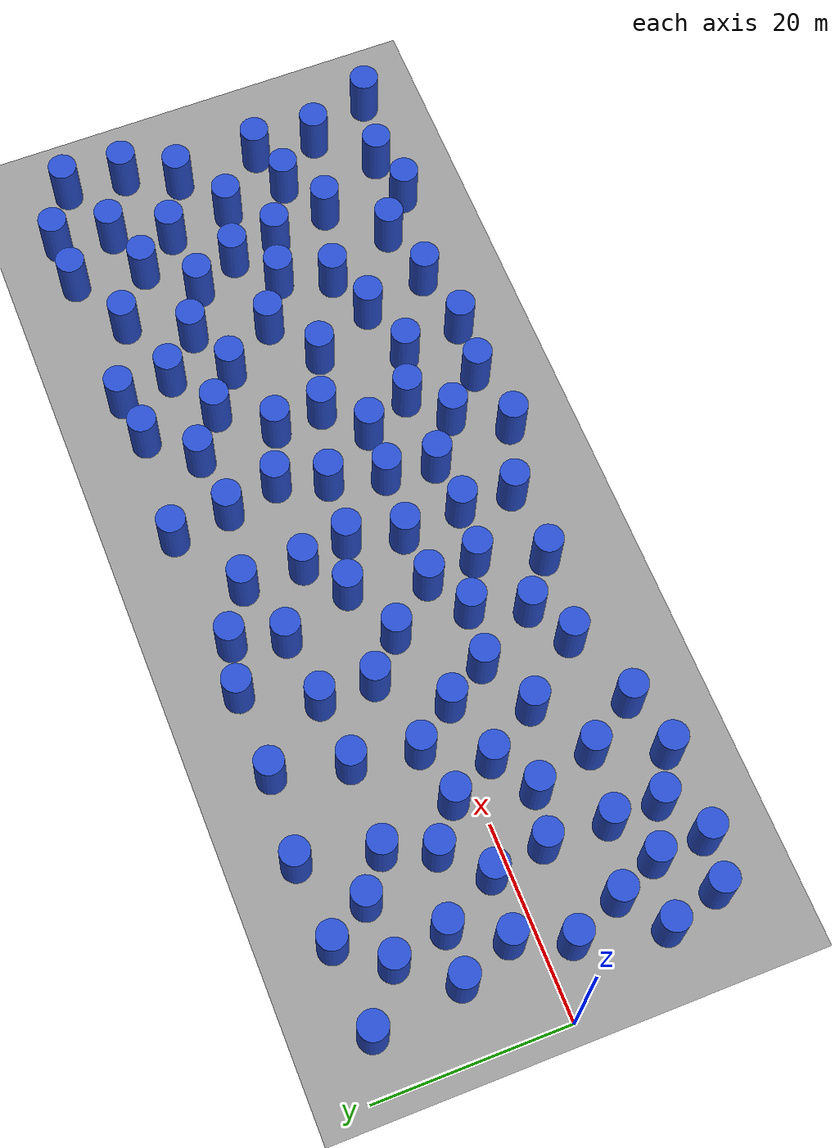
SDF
<sdf version="1.7">
 <world name="default">
  <plugin name="disable_physics" filename="libdisable_physics.so"/>
  <plugin name="gazebo_ros_state" filename="libgazebo_ros_state.so">
   <ros>
    <namespace>/plug</namespace>
    <argument>model_states:=model_states_plug</argument>
    <argument>link_states:=link_states_plug</argument>
   </ros>
   <update_rate>100.0</update_rate>
  </plugin>
  <light name="sun" type="directional">
   <pose>0 0 10 0 -0 0</pose>
   <diffuse>0.8 0.8 0.8 1</diffuse>
   <specular>0.2 0.2 0.2 1</specular>
   <attenuation>
    <range>1000</range>
    <constant>0.9</constant>
    <linear>0.01</linear>
    <quadratic>0.001</quadratic>
   </attenuation>
   <direction>-0.5 0.1 -0.9</direction>
   <spot><inner_angle>0</inner_angle><outer_angle>0</outer_angle><falloff>0</falloff></spot>
  </light>
  <gravity>0 0 -9.8</gravity>
  <magnetic_field>6e-06 2.3e-05 -4.2e-05</magnetic_field>
  <atmosphere type="adiabatic"/>
  <physics type="ode">
   <max_step_size>0.001</max_step_size>
   <real_time_factor>1</real_time_factor>
   <real_time_update_rate>1000</real_time_update_rate>
  </physics>
  <scene><ambient>0.4 0.4 0.4 1</ambient><background>0.7 0.7 0.7 1</background><shadows>1</shadows></scene>
  <audio><device>default</device></audio>
  <spherical_coordinates>
   <surface_model>EARTH_WGS84</surface_model>
   <latitude_deg>0</latitude_deg>
   <longitude_deg>0</longitude_deg>
   <elevation>0</elevation>
   <heading_deg>0</heading_deg>
  </spherical_coordinates>
  <model name="ground_plane_map">
   <static>1</static>
   <link name="link">
    <collision name="collision">
     <geometry><plane><normal>0 0 1</normal><size>110 50</size></plane></geometry>
     <surface>
      <contact><collide_without_contact>1</collide_without_contact></contact>
      <friction><ode><mu>100</mu><mu2>50</mu2></ode></friction>
     </surface>
    </collision>
    <visual name="visual">
     <cast_shadows>0</cast_shadows>
     <geometry><plane><normal>0 0 1</normal><size>110 50</size></plane></geometry>
     <material>
      <script><uri>file://media/materials/scripts/gazebo.material</uri><name>Gazebo/Grey</name></script>
     </material>
    </visual>
   </link>
   <pose>53 0 0 0 -0 0</pose>
  </model>
  <model name="0">
   <static>1</static>
   <link name="link">
    <inertial>
     <mass>2</mass>
     <inertia><ixx>7.125</ixx><ixy>0</ixy><ixz>0</ixz><iyy>7.125</iyy><iyz>0</iyz><izz>2.25</izz></inertia>
    </inertial>
    <collision name="collision">
     <geometry><cylinder><length>6</length><radius>1.5</radius></cylinder></geometry>
     <surface><contact><collide_without_contact>1</collide_without_contact></contact></surface>
    </collision>
    <visual name="visual">
     <geometry><cylinder><length>6</length><radius>1.5</radius></cylinder></geometry>
     <material>
      <script><uri>file://media/materials/scripts/gazebo.material</uri><name>Gazebo/Blue</name></script>
     </material>
    </visual>
    <gravity>0</gravity>
   </link>
   <pose>45.2954 -8.92008 3 0 -0 0</pose>
  </model>
  <model name="1">
   <static>1</static>
   <link name="link">
    <inertial>
     <mass>2</mass>
     <inertia><ixx>7.125</ixx><ixy>0</ixy><ixz>0</ixz><iyy>7.125</iyy><iyz>0</iyz><izz>2.25</izz></inertia>
    </inertial>
    <collision name="collision">
     <geometry><cylinder><length>6</length><radius>1.5</radius></cylinder></geometry>
     <surface><contact><collide_without_contact>1</collide_without_contact></contact></surface>
    </collision>
    <visual name="visual">
     <geometry><cylinder><length>6</length><radius>1.5</radius></cylinder></geometry>
     <material>
      <script><uri>file://media/materials/scripts/gazebo.material</uri><name>Gazebo/Blue</name></script>
     </material>
    </visual>
    <gravity>0</gravity>
   </link>
   <pose>80.5285 -7.27743 3 0 -0 0</pose>
  </model>
  <model name="2">
   <static>1</static>
   <link name="link">
    <inertial>
     <mass>2</mass>
     <inertia><ixx>7.125</ixx><ixy>0</ixy><ixz>0</ixz><iyy>7.125</iyy><iyz>0</iyz><izz>2.25</izz></inertia>
    </inertial>
    <collision name="collision">
     <geometry><cylinder><length>6</length><radius>1.5</radius></cylinder></geometry>
     <surface><contact><collide_without_contact>1</collide_without_contact></contact></surface>
    </collision>
    <visual name="visual">
     <geometry><cylinder><length>6</length><radius>1.5</radius></cylinder></geometry>
     <material>
      <script><uri>file://media/materials/scripts/gazebo.material</uri><name>Gazebo/Blue</name></script>
     </material>
    </visual>
    <gravity>0</gravity>
   </link>
   <pose>92.587 0.173414 3 0 -0 0</pose>
  </model>
  <model name="3">
   <static>1</static>
   <link name="link">
    <inertial>
     <mass>2</mass>
     <inertia><ixx>7.125</ixx><ixy>0</ixy><ixz>0</ixz><iyy>7.125</iyy><iyz>0</iyz><izz>2.25</izz></inertia>
    </inertial>
    <collision name="collision">
     <geometry><cylinder><length>6</length><radius>1.5</radius></cylinder></geometry>
     <surface><contact><collide_without_contact>1</collide_without_contact></contact></surface>
    </collision>
    <visual name="visual">
     <geometry><cylinder><length>6</length><radius>1.5</radius></cylinder></geometry>
     <material>
      <script><uri>file://media/materials/scripts/gazebo.material</uri><name>Gazebo/Blue</name></script>
     </material>
    </visual>
    <gravity>0</gravity>
   </link>
   <pose>64.4818 -9.23127 3 0 -0 0</pose>
  </model>
  <model name="4">
   <static>1</static>
   <link name="link">
    <inertial>
     <mass>2</mass>
     <inertia><ixx>7.125</ixx><ixy>0</ixy><ixz>0</ixz><iyy>7.125</iyy><iyz>0</iyz><izz>2.25</izz></inertia>
    </inertial>
    <collision name="collision">
     <geometry><cylinder><length>6</length><radius>1.5</radius></cylinder></geometry>
     <surface><contact><collide_without_contact>1</collide_without_contact></contact></surface>
    </collision>
    <visual name="visual">
     <geometry><cylinder><length>6</length><radius>1.5</radius></cylinder></geometry>
     <material>
      <script><uri>file://media/materials/scripts/gazebo.material</uri><name>Gazebo/Blue</name></script>
     </material>
    </visual>
    <gravity>0</gravity>
   </link>
   <pose>83.0911 14.8801 3 0 -0 0</pose>
  </model>
  <model name="5">
   <static>1</static>
   <link name="link">
    <inertial>
     <mass>2</mass>
     <inertia><ixx>7.125</ixx><ixy>0</ixy><ixz>0</ixz><iyy>7.125</iyy><iyz>0</iyz><izz>2.25</izz></inertia>
    </inertial>
    <collision name="collision">
     <geometry><cylinder><length>6</length><radius>1.5</radius></cylinder></geometry>
     <surface><contact><collide_without_contact>1</collide_without_contact></contact></surface>
    </collision>
    <visual name="visual">
     <geometry><cylinder><length>6</length><radius>1.5</radius></cylinder></geometry>
     <material>
      <script><uri>file://media/materials/scripts/gazebo.material</uri><name>Gazebo/Blue</name></script>
     </material>
    </visual>
    <gravity>0</gravity>
   </link>
   <pose>91.6873 6.80741 3 0 -0 0</pose>
  </model>
  <model name="6">
   <static>1</static>
   <link name="link">
    <inertial>
     <mass>2</mass>
     <inertia><ixx>7.125</ixx><ixy>0</ixy><ixz>0</ixz><iyy>7.125</iyy><iyz>0</iyz><izz>2.25</izz></inertia>
    </inertial>
    <collision name="collision">
     <geometry><cylinder><length>6</length><radius>1.5</radius></cylinder></geometry>
     <surface><contact><collide_without_contact>1</collide_without_contact></contact></surface>
    </collision>
    <visual name="visual">
     <geometry><cylinder><length>6</length><radius>1.5</radius></cylinder></geometry>
     <material>
      <script><uri>file://media/materials/scripts/gazebo.material</uri><name>Gazebo/Blue</name></script>
     </material>
    </visual>
    <gravity>0</gravity>
   </link>
   <pose>46.6147 4.10282 3 0 -0 0</pose>
  </model>
  <model name="7">
   <static>1</static>
   <link name="link">
    <inertial>
     <mass>2</mass>
     <inertia><ixx>7.125</ixx><ixy>0</ixy><ixz>0</ixz><iyy>7.125</iyy><iyz>0</iyz><izz>2.25</izz></inertia>
    </inertial>
    <collision name="collision">
     <geometry><cylinder><length>6</length><radius>1.5</radius></cylinder></geometry>
     <surface><contact><collide_without_contact>1</collide_without_contact></contact></surface>
    </collision>
    <visual name="visual">
     <geometry><cylinder><length>6</length><radius>1.5</radius></cylinder></geometry>
     <material>
      <script><uri>file://media/materials/scripts/gazebo.material</uri><name>Gazebo/Blue</name></script>
     </material>
    </visual>
    <gravity>0</gravity>
   </link>
   <pose>50.7699 13.5165 3 0 -0 0</pose>
  </model>
  <model name="8">
   <static>1</static>
   <link name="link">
    <inertial>
     <mass>2</mass>
     <inertia><ixx>7.125</ixx><ixy>0</ixy><ixz>0</ixz><iyy>7.125</iyy><iyz>0</iyz><izz>2.25</izz></inertia>
    </inertial>
    <collision name="collision">
     <geometry><cylinder><length>6</length><radius>1.5</radius></cylinder></geometry>
     <surface><contact><collide_without_contact>1</collide_without_contact></contact></surface>
    </collision>
    <visual name="visual">
     <geometry><cylinder><length>6</length><radius>1.5</radius></cylinder></geometry>
     <material>
      <script><uri>file://media/materials/scripts/gazebo.material</uri><name>Gazebo/Blue</name></script>
     </material>
    </visual>
    <gravity>0</gravity>
   </link>
   <pose>57.7238 -17.9805 3 0 -0 0</pose>
  </model>
  <model name="9">
   <static>1</static>
   <link name="link">
    <inertial>
     <mass>2</mass>
     <inertia><ixx>7.125</ixx><ixy>0</ixy><ixz>0</ixz><iyy>7.125</iyy><iyz>0</iyz><izz>2.25</izz></inertia>
    </inertial>
    <collision name="collision">
     <geometry><cylinder><length>6</length><radius>1.5</radius></cylinder></geometry>
     <surface><contact><collide_without_contact>1</collide_without_contact></contact></surface>
    </collision>
    <visual name="visual">
     <geometry><cylinder><length>6</length><radius>1.5</radius></cylinder></geometry>
     <material>
      <script><uri>file://media/materials/scripts/gazebo.material</uri><name>Gazebo/Blue</name></script>
     </material>
    </visual>
    <gravity>0</gravity>
   </link>
   <pose>84.51 6.22167 3 0 -0 0</pose>
  </model>
  <model name="10">
   <static>1</static>
   <link name="link">
    <inertial>
     <mass>2</mass>
     <inertia><ixx>7.125</ixx><ixy>0</ixy><ixz>0</ixz><iyy>7.125</iyy><iyz>0</iyz><izz>2.25</izz></inertia>
    </inertial>
    <collision name="collision">
     <geometry><cylinder><length>6</length><radius>1.5</radius></cylinder></geometry>
     <surface><contact><collide_without_contact>1</collide_without_contact></contact></surface>
    </collision>
    <visual name="visual">
     <geometry><cylinder><length>6</length><radius>1.5</radius></cylinder></geometry>
     <material>
      <script><uri>file://media/materials/scripts/gazebo.material</uri><name>Gazebo/Blue</name></script>
     </material>
    </visual>
    <gravity>0</gravity>
   </link>
   <pose>88.6575 -9.4753 3 0 -0 0</pose>
  </model>
  <model name="11">
   <static>1</static>
   <link name="link">
    <inertial>
     <mass>2</mass>
     <inertia><ixx>7.125</ixx><ixy>0</ixy><ixz>0</ixz><iyy>7.125</iyy><iyz>0</iyz><izz>2.25</izz></inertia>
    </inertial>
    <collision name="collision">
     <geometry><cylinder><length>6</length><radius>1.5</radius></cylinder></geometry>
     <surface><contact><collide_without_contact>1</collide_without_contact></contact></surface>
    </collision>
    <visual name="visual">
     <geometry><cylinder><length>6</length><radius>1.5</radius></cylinder></geometry>
     <material>
      <script><uri>file://media/materials/scripts/gazebo.material</uri><name>Gazebo/Blue</name></script>
     </material>
    </visual>
    <gravity>0</gravity>
   </link>
   <pose>23.0335 2.4979 3 0 -0 0</pose>
  </model>
  <model name="12">
   <static>1</static>
   <link name="link">
    <inertial>
     <mass>2</mass>
     <inertia><ixx>7.125</ixx><ixy>0</ixy><ixz>0</ixz><iyy>7.125</iyy><iyz>0</iyz><izz>2.25</izz></inertia>
    </inertial>
    <collision name="collision">
     <geometry><cylinder><length>6</length><radius>1.5</radius></cylinder></geometry>
     <surface><contact><collide_without_contact>1</collide_without_contact></contact></surface>
    </collision>
    <visual name="visual">
     <geometry><cylinder><length>6</length><radius>1.5</radius></cylinder></geometry>
     <material>
      <script><uri>file://media/materials/scripts/gazebo.material</uri><name>Gazebo/Blue</name></script>
     </material>
    </visual>
    <gravity>0</gravity>
   </link>
   <pose>82.4084 -1.92513 3 0 -0 0</pose>
  </model>
  <model name="13">
   <static>1</static>
   <link name="link">
    <inertial>
     <mass>2</mass>
     <inertia><ixx>7.125</ixx><ixy>0</ixy><ixz>0</ixz><iyy>7.125</iyy><iyz>0</iyz><izz>2.25</izz></inertia>
    </inertial>
    <collision name="collision">
     <geometry><cylinder><length>6</length><radius>1.5</radius></cylinder></geometry>
     <surface><contact><collide_without_contact>1</collide_without_contact></contact></surface>
    </collision>
    <visual name="visual">
     <geometry><cylinder><length>6</length><radius>1.5</radius></cylinder></geometry>
     <material>
      <script><uri>file://media/materials/scripts/gazebo.material</uri><name>Gazebo/Blue</name></script>
     </material>
    </visual>
    <gravity>0</gravity>
   </link>
   <pose>15.0786 1.89689 3 0 -0 0</pose>
  </model>
  <model name="14">
   <static>1</static>
   <link name="link">
    <inertial>
     <mass>2</mass>
     <inertia><ixx>7.125</ixx><ixy>0</ixy><ixz>0</ixz><iyy>7.125</iyy><iyz>0</iyz><izz>2.25</izz></inertia>
    </inertial>
    <collision name="collision">
     <geometry><cylinder><length>6</length><radius>1.5</radius></cylinder></geometry>
     <surface><contact><collide_without_contact>1</collide_without_contact></contact></surface>
    </collision>
    <visual name="visual">
     <geometry><cylinder><length>6</length><radius>1.5</radius></cylinder></geometry>
     <material>
      <script><uri>file://media/materials/scripts/gazebo.material</uri><name>Gazebo/Blue</name></script>
     </material>
    </visual>
    <gravity>0</gravity>
   </link>
   <pose>97.9923 3.81787 3 0 -0 0</pose>
  </model>
  <model name="15">
   <static>1</static>
   <link name="link">
    <inertial>
     <mass>2</mass>
     <inertia><ixx>7.125</ixx><ixy>0</ixy><ixz>0</ixz><iyy>7.125</iyy><iyz>0</iyz><izz>2.25</izz></inertia>
    </inertial>
    <collision name="collision">
     <geometry><cylinder><length>6</length><radius>1.5</radius></cylinder></geometry>
     <surface><contact><collide_without_contact>1</collide_without_contact></contact></surface>
    </collision>
    <visual name="visual">
     <geometry><cylinder><length>6</length><radius>1.5</radius></cylinder></geometry>
     <material>
      <script><uri>file://media/materials/scripts/gazebo.material</uri><name>Gazebo/Blue</name></script>
     </material>
    </visual>
    <gravity>0</gravity>
   </link>
   <pose>62.3398 -4.25866 3 0 -0 0</pose>
  </model>
  <model name="16">
   <static>1</static>
   <link name="link">
    <inertial>
     <mass>2</mass>
     <inertia><ixx>7.125</ixx><ixy>0</ixy><ixz>0</ixz><iyy>7.125</iyy><iyz>0</iyz><izz>2.25</izz></inertia>
    </inertial>
    <collision name="collision">
     <geometry><cylinder><length>6</length><radius>1.5</radius></cylinder></geometry>
     <surface><contact><collide_without_contact>1</collide_without_contact></contact></surface>
    </collision>
    <visual name="visual">
     <geometry><cylinder><length>6</length><radius>1.5</radius></cylinder></geometry>
     <material>
      <script><uri>file://media/materials/scripts/gazebo.material</uri><name>Gazebo/Blue</name></script>
     </material>
    </visual>
    <gravity>0</gravity>
   </link>
   <pose>22.871 -11.591 3 0 -0 0</pose>
  </model>
  <model name="17">
   <static>1</static>
   <link name="link">
    <inertial>
     <mass>2</mass>
     <inertia><ixx>7.125</ixx><ixy>0</ixy><ixz>0</ixz><iyy>7.125</iyy><iyz>0</iyz><izz>2.25</izz></inertia>
    </inertial>
    <collision name="collision">
     <geometry><cylinder><length>6</length><radius>1.5</radius></cylinder></geometry>
     <surface><contact><collide_without_contact>1</collide_without_contact></contact></surface>
    </collision>
    <visual name="visual">
     <geometry><cylinder><length>6</length><radius>1.5</radius></cylinder></geometry>
     <material>
      <script><uri>file://media/materials/scripts/gazebo.material</uri><name>Gazebo/Blue</name></script>
     </material>
    </visual>
    <gravity>0</gravity>
   </link>
   <pose>50.7235 -15.1765 3 0 -0 0</pose>
  </model>
  <model name="18">
   <static>1</static>
   <link name="link">
    <inertial>
     <mass>2</mass>
     <inertia><ixx>7.125</ixx><ixy>0</ixy><ixz>0</ixz><iyy>7.125</iyy><iyz>0</iyz><izz>2.25</izz></inertia>
    </inertial>
    <collision name="collision">
     <geometry><cylinder><length>6</length><radius>1.5</radius></cylinder></geometry>
     <surface><contact><collide_without_contact>1</collide_without_contact></contact></surface>
    </collision>
    <visual name="visual">
     <geometry><cylinder><length>6</length><radius>1.5</radius></cylinder></geometry>
     <material>
      <script><uri>file://media/materials/scripts/gazebo.material</uri><name>Gazebo/Blue</name></script>
     </material>
    </visual>
    <gravity>0</gravity>
   </link>
   <pose>94.068 12.671 3 0 -0 0</pose>
  </model>
  <model name="19">
   <static>1</static>
   <link name="link">
    <inertial>
     <mass>2</mass>
     <inertia><ixx>7.125</ixx><ixy>0</ixy><ixz>0</ixz><iyy>7.125</iyy><iyz>0</iyz><izz>2.25</izz></inertia>
    </inertial>
    <collision name="collision">
     <geometry><cylinder><length>6</length><radius>1.5</radius></cylinder></geometry>
     <surface><contact><collide_without_contact>1</collide_without_contact></contact></surface>
    </collision>
    <visual name="visual">
     <geometry><cylinder><length>6</length><radius>1.5</radius></cylinder></geometry>
     <material>
      <script><uri>file://media/materials/scripts/gazebo.material</uri><name>Gazebo/Blue</name></script>
     </material>
    </visual>
    <gravity>0</gravity>
   </link>
   <pose>56.9382 -4.02205 3 0 -0 0</pose>
  </model>
  <model name="20">
   <static>1</static>
   <link name="link">
    <inertial>
     <mass>2</mass>
     <inertia><ixx>7.125</ixx><ixy>0</ixy><ixz>0</ixz><iyy>7.125</iyy><iyz>0</iyz><izz>2.25</izz></inertia>
    </inertial>
    <collision name="collision">
     <geometry><cylinder><length>6</length><radius>1.5</radius></cylinder></geometry>
     <surface><contact><collide_without_contact>1</collide_without_contact></contact></surface>
    </collision>
    <visual name="visual">
     <geometry><cylinder><length>6</length><radius>1.5</radius></cylinder></geometry>
     <material>
      <script><uri>file://media/materials/scripts/gazebo.material</uri><name>Gazebo/Blue</name></script>
     </material>
    </visual>
    <gravity>0</gravity>
   </link>
   <pose>101.137 15.4268 3 0 -0 0</pose>
  </model>
  <model name="21">
   <static>1</static>
   <link name="link">
    <inertial>
     <mass>2</mass>
     <inertia><ixx>7.125</ixx><ixy>0</ixy><ixz>0</ixz><iyy>7.125</iyy><iyz>0</iyz><izz>2.25</izz></inertia>
    </inertial>
    <collision name="collision">
     <geometry><cylinder><length>6</length><radius>1.5</radius></cylinder></geometry>
     <surface><contact><collide_without_contact>1</collide_without_contact></contact></surface>
    </collision>
    <visual name="visual">
     <geometry><cylinder><length>6</length><radius>1.5</radius></cylinder></geometry>
     <material>
      <script><uri>file://media/materials/scripts/gazebo.material</uri><name>Gazebo/Blue</name></script>
     </material>
    </visual>
    <gravity>0</gravity>
   </link>
   <pose>65.6243 12.7679 3 0 -0 0</pose>
  </model>
  <model name="22">
   <static>1</static>
   <link name="link">
    <inertial>
     <mass>2</mass>
     <inertia><ixx>7.125</ixx><ixy>0</ixy><ixz>0</ixz><iyy>7.125</iyy><iyz>0</iyz><izz>2.25</izz></inertia>
    </inertial>
    <collision name="collision">
     <geometry><cylinder><length>6</length><radius>1.5</radius></cylinder></geometry>
     <surface><contact><collide_without_contact>1</collide_without_contact></contact></surface>
    </collision>
    <visual name="visual">
     <geometry><cylinder><length>6</length><radius>1.5</radius></cylinder></geometry>
     <material>
      <script><uri>file://media/materials/scripts/gazebo.material</uri><name>Gazebo/Blue</name></script>
     </material>
    </visual>
    <gravity>0</gravity>
   </link>
   <pose>15.862 -10.343 3 0 -0 0</pose>
  </model>
  <model name="23">
   <static>1</static>
   <link name="link">
    <inertial>
     <mass>2</mass>
     <inertia><ixx>7.125</ixx><ixy>0</ixy><ixz>0</ixz><iyy>7.125</iyy><iyz>0</iyz><izz>2.25</izz></inertia>
    </inertial>
    <collision name="collision">
     <geometry><cylinder><length>6</length><radius>1.5</radius></cylinder></geometry>
     <surface><contact><collide_without_contact>1</collide_without_contact></contact></surface>
    </collision>
    <visual name="visual">
     <geometry><cylinder><length>6</length><radius>1.5</radius></cylinder></geometry>
     <material>
      <script><uri>file://media/materials/scripts/gazebo.material</uri><name>Gazebo/Blue</name></script>
     </material>
    </visual>
    <gravity>0</gravity>
   </link>
   <pose>83.6436 -14.7775 3 0 -0 0</pose>
  </model>
  <model name="24">
   <static>1</static>
   <link name="link">
    <inertial>
     <mass>2</mass>
     <inertia><ixx>7.125</ixx><ixy>0</ixy><ixz>0</ixz><iyy>7.125</iyy><iyz>0</iyz><izz>2.25</izz></inertia>
    </inertial>
    <collision name="collision">
     <geometry><cylinder><length>6</length><radius>1.5</radius></cylinder></geometry>
     <surface><contact><collide_without_contact>1</collide_without_contact></contact></surface>
    </collision>
    <visual name="visual">
     <geometry><cylinder><length>6</length><radius>1.5</radius></cylinder></geometry>
     <material>
      <script><uri>file://media/materials/scripts/gazebo.material</uri><name>Gazebo/Blue</name></script>
     </material>
    </visual>
    <gravity>0</gravity>
   </link>
   <pose>8.88771 2.73304 3 0 -0 0</pose>
  </model>
  <model name="25">
   <static>1</static>
   <link name="link">
    <inertial>
     <mass>2</mass>
     <inertia><ixx>7.125</ixx><ixy>0</ixy><ixz>0</ixz><iyy>7.125</iyy><iyz>0</iyz><izz>2.25</izz></inertia>
    </inertial>
    <collision name="collision">
     <geometry><cylinder><length>6</length><radius>1.5</radius></cylinder></geometry>
     <surface><contact><collide_without_contact>1</collide_without_contact></contact></surface>
    </collision>
    <visual name="visual">
     <geometry><cylinder><length>6</length><radius>1.5</radius></cylinder></geometry>
     <material>
      <script><uri>file://media/materials/scripts/gazebo.material</uri><name>Gazebo/Blue</name></script>
     </material>
    </visual>
    <gravity>0</gravity>
   </link>
   <pose>70.5171 -17.5122 3 0 -0 0</pose>
  </model>
  <model name="26">
   <static>1</static>
   <link name="link">
    <inertial>
     <mass>2</mass>
     <inertia><ixx>7.125</ixx><ixy>0</ixy><ixz>0</ixz><iyy>7.125</iyy><iyz>0</iyz><izz>2.25</izz></inertia>
    </inertial>
    <collision name="collision">
     <geometry><cylinder><length>6</length><radius>1.5</radius></cylinder></geometry>
     <surface><contact><collide_without_contact>1</collide_without_contact></contact></surface>
    </collision>
    <visual name="visual">
     <geometry><cylinder><length>6</length><radius>1.5</radius></cylinder></geometry>
     <material>
      <script><uri>file://media/materials/scripts/gazebo.material</uri><name>Gazebo/Blue</name></script>
     </material>
    </visual>
    <gravity>0</gravity>
   </link>
   <pose>40.4036 17.7791 3 0 -0 0</pose>
  </model>
  <model name="27">
   <static>1</static>
   <link name="link">
    <inertial>
     <mass>2</mass>
     <inertia><ixx>7.125</ixx><ixy>0</ixy><ixz>0</ixz><iyy>7.125</iyy><iyz>0</iyz><izz>2.25</izz></inertia>
    </inertial>
    <collision name="collision">
     <geometry><cylinder><length>6</length><radius>1.5</radius></cylinder></geometry>
     <surface><contact><collide_without_contact>1</collide_without_contact></contact></surface>
    </collision>
    <visual name="visual">
     <geometry><cylinder><length>6</length><radius>1.5</radius></cylinder></geometry>
     <material>
      <script><uri>file://media/materials/scripts/gazebo.material</uri><name>Gazebo/Blue</name></script>
     </material>
    </visual>
    <gravity>0</gravity>
   </link>
   <pose>97.72 -11.656 3 0 -0 0</pose>
  </model>
  <model name="28">
   <static>1</static>
   <link name="link">
    <inertial>
     <mass>2</mass>
     <inertia><ixx>7.125</ixx><ixy>0</ixy><ixz>0</ixz><iyy>7.125</iyy><iyz>0</iyz><izz>2.25</izz></inertia>
    </inertial>
    <collision name="collision">
     <geometry><cylinder><length>6</length><radius>1.5</radius></cylinder></geometry>
     <surface><contact><collide_without_contact>1</collide_without_contact></contact></surface>
    </collision>
    <visual name="visual">
     <geometry><cylinder><length>6</length><radius>1.5</radius></cylinder></geometry>
     <material>
      <script><uri>file://media/materials/scripts/gazebo.material</uri><name>Gazebo/Blue</name></script>
     </material>
    </visual>
    <gravity>0</gravity>
   </link>
   <pose>6.70991 -2.7521 3 0 -0 0</pose>
  </model>
  <model name="29">
   <static>1</static>
   <link name="link">
    <inertial>
     <mass>2</mass>
     <inertia><ixx>7.125</ixx><ixy>0</ixy><ixz>0</ixz><iyy>7.125</iyy><iyz>0</iyz><izz>2.25</izz></inertia>
    </inertial>
    <collision name="collision">
     <geometry><cylinder><length>6</length><radius>1.5</radius></cylinder></geometry>
     <surface><contact><collide_without_contact>1</collide_without_contact></contact></surface>
    </collision>
    <visual name="visual">
     <geometry><cylinder><length>6</length><radius>1.5</radius></cylinder></geometry>
     <material>
      <script><uri>file://media/materials/scripts/gazebo.material</uri><name>Gazebo/Blue</name></script>
     </material>
    </visual>
    <gravity>0</gravity>
   </link>
   <pose>38.4785 -11.8282 3 0 -0 0</pose>
  </model>
  <model name="30">
   <static>1</static>
   <link name="link">
    <inertial>
     <mass>2</mass>
     <inertia><ixx>7.125</ixx><ixy>0</ixy><ixz>0</ixz><iyy>7.125</iyy><iyz>0</iyz><izz>2.25</izz></inertia>
    </inertial>
    <collision name="collision">
     <geometry><cylinder><length>6</length><radius>1.5</radius></cylinder></geometry>
     <surface><contact><collide_without_contact>1</collide_without_contact></contact></surface>
    </collision>
    <visual name="visual">
     <geometry><cylinder><length>6</length><radius>1.5</radius></cylinder></geometry>
     <material>
      <script><uri>file://media/materials/scripts/gazebo.material</uri><name>Gazebo/Blue</name></script>
     </material>
    </visual>
    <gravity>0</gravity>
   </link>
   <pose>14.2894 18.0647 3 0 -0 0</pose>
  </model>
  <model name="31">
   <static>1</static>
   <link name="link">
    <inertial>
     <mass>2</mass>
     <inertia><ixx>7.125</ixx><ixy>0</ixy><ixz>0</ixz><iyy>7.125</iyy><iyz>0</iyz><izz>2.25</izz></inertia>
    </inertial>
    <collision name="collision">
     <geometry><cylinder><length>6</length><radius>1.5</radius></cylinder></geometry>
     <surface><contact><collide_without_contact>1</collide_without_contact></contact></surface>
    </collision>
    <visual name="visual">
     <geometry><cylinder><length>6</length><radius>1.5</radius></cylinder></geometry>
     <material>
      <script><uri>file://media/materials/scripts/gazebo.material</uri><name>Gazebo/Blue</name></script>
     </material>
    </visual>
    <gravity>0</gravity>
   </link>
   <pose>75.465 12.5181 3 0 -0 0</pose>
  </model>
  <model name="32">
   <static>1</static>
   <link name="link">
    <inertial>
     <mass>2</mass>
     <inertia><ixx>7.125</ixx><ixy>0</ixy><ixz>0</ixz><iyy>7.125</iyy><iyz>0</iyz><izz>2.25</izz></inertia>
    </inertial>
    <collision name="collision">
     <geometry><cylinder><length>6</length><radius>1.5</radius></cylinder></geometry>
     <surface><contact><collide_without_contact>1</collide_without_contact></contact></surface>
    </collision>
    <visual name="visual">
     <geometry><cylinder><length>6</length><radius>1.5</radius></cylinder></geometry>
     <material>
      <script><uri>file://media/materials/scripts/gazebo.material</uri><name>Gazebo/Blue</name></script>
     </material>
    </visual>
    <gravity>0</gravity>
   </link>
   <pose>69.7461 17.2623 3 0 -0 0</pose>
  </model>
  <model name="33">
   <static>1</static>
   <link name="link">
    <inertial>
     <mass>2</mass>
     <inertia><ixx>7.125</ixx><ixy>0</ixy><ixz>0</ixz><iyy>7.125</iyy><iyz>0</iyz><izz>2.25</izz></inertia>
    </inertial>
    <collision name="collision">
     <geometry><cylinder><length>6</length><radius>1.5</radius></cylinder></geometry>
     <surface><contact><collide_without_contact>1</collide_without_contact></contact></surface>
    </collision>
    <visual name="visual">
     <geometry><cylinder><length>6</length><radius>1.5</radius></cylinder></geometry>
     <material>
      <script><uri>file://media/materials/scripts/gazebo.material</uri><name>Gazebo/Blue</name></script>
     </material>
    </visual>
    <gravity>0</gravity>
   </link>
   <pose>28.8167 3.58128 3 0 -0 0</pose>
  </model>
  <model name="34">
   <static>1</static>
   <link name="link">
    <inertial>
     <mass>2</mass>
     <inertia><ixx>7.125</ixx><ixy>0</ixy><ixz>0</ixz><iyy>7.125</iyy><iyz>0</iyz><izz>2.25</izz></inertia>
    </inertial>
    <collision name="collision">
     <geometry><cylinder><length>6</length><radius>1.5</radius></cylinder></geometry>
     <surface><contact><collide_without_contact>1</collide_without_contact></contact></surface>
    </collision>
    <visual name="visual">
     <geometry><cylinder><length>6</length><radius>1.5</radius></cylinder></geometry>
     <material>
      <script><uri>file://media/materials/scripts/gazebo.material</uri><name>Gazebo/Blue</name></script>
     </material>
    </visual>
    <gravity>0</gravity>
   </link>
   <pose>50.2477 -3.3335 3 0 -0 0</pose>
  </model>
  <model name="35">
   <static>1</static>
   <link name="link">
    <inertial>
     <mass>2</mass>
     <inertia><ixx>7.125</ixx><ixy>0</ixy><ixz>0</ixz><iyy>7.125</iyy><iyz>0</iyz><izz>2.25</izz></inertia>
    </inertial>
    <collision name="collision">
     <geometry><cylinder><length>6</length><radius>1.5</radius></cylinder></geometry>
     <surface><contact><collide_without_contact>1</collide_without_contact></contact></surface>
    </collision>
    <visual name="visual">
     <geometry><cylinder><length>6</length><radius>1.5</radius></cylinder></geometry>
     <material>
      <script><uri>file://media/materials/scripts/gazebo.material</uri><name>Gazebo/Blue</name></script>
     </material>
    </visual>
    <gravity>0</gravity>
   </link>
   <pose>34.7103 -5.28539 3 0 -0 0</pose>
  </model>
  <model name="36">
   <static>1</static>
   <link name="link">
    <inertial>
     <mass>2</mass>
     <inertia><ixx>7.125</ixx><ixy>0</ixy><ixz>0</ixz><iyy>7.125</iyy><iyz>0</iyz><izz>2.25</izz></inertia>
    </inertial>
    <collision name="collision">
     <geometry><cylinder><length>6</length><radius>1.5</radius></cylinder></geometry>
     <surface><contact><collide_without_contact>1</collide_without_contact></contact></surface>
    </collision>
    <visual name="visual">
     <geometry><cylinder><length>6</length><radius>1.5</radius></cylinder></geometry>
     <material>
      <script><uri>file://media/materials/scripts/gazebo.material</uri><name>Gazebo/Blue</name></script>
     </material>
    </visual>
    <gravity>0</gravity>
   </link>
   <pose>8.93256 -8.10732 3 0 -0 0</pose>
  </model>
  <model name="37">
   <static>1</static>
   <link name="link">
    <inertial>
     <mass>2</mass>
     <inertia><ixx>7.125</ixx><ixy>0</ixy><ixz>0</ixz><iyy>7.125</iyy><iyz>0</iyz><izz>2.25</izz></inertia>
    </inertial>
    <collision name="collision">
     <geometry><cylinder><length>6</length><radius>1.5</radius></cylinder></geometry>
     <surface><contact><collide_without_contact>1</collide_without_contact></contact></surface>
    </collision>
    <visual name="visual">
     <geometry><cylinder><length>6</length><radius>1.5</radius></cylinder></geometry>
     <material>
      <script><uri>file://media/materials/scripts/gazebo.material</uri><name>Gazebo/Blue</name></script>
     </material>
    </visual>
    <gravity>0</gravity>
   </link>
   <pose>65.9735 4.47984 3 0 -0 0</pose>
  </model>
  <model name="38">
   <static>1</static>
   <link name="link">
    <inertial>
     <mass>2</mass>
     <inertia><ixx>7.125</ixx><ixy>0</ixy><ixz>0</ixz><iyy>7.125</iyy><iyz>0</iyz><izz>2.25</izz></inertia>
    </inertial>
    <collision name="collision">
     <geometry><cylinder><length>6</length><radius>1.5</radius></cylinder></geometry>
     <surface><contact><collide_without_contact>1</collide_without_contact></contact></surface>
    </collision>
    <visual name="visual">
     <geometry><cylinder><length>6</length><radius>1.5</radius></cylinder></geometry>
     <material>
      <script><uri>file://media/materials/scripts/gazebo.material</uri><name>Gazebo/Blue</name></script>
     </material>
    </visual>
    <gravity>0</gravity>
   </link>
   <pose>4.64785 -11.3845 3 0 -0 0</pose>
  </model>
  <model name="39">
   <static>1</static>
   <link name="link">
    <inertial>
     <mass>2</mass>
     <inertia><ixx>7.125</ixx><ixy>0</ixy><ixz>0</ixz><iyy>7.125</iyy><iyz>0</iyz><izz>2.25</izz></inertia>
    </inertial>
    <collision name="collision">
     <geometry><cylinder><length>6</length><radius>1.5</radius></cylinder></geometry>
     <surface><contact><collide_without_contact>1</collide_without_contact></contact></surface>
    </collision>
    <visual name="visual">
     <geometry><cylinder><length>6</length><radius>1.5</radius></cylinder></geometry>
     <material>
      <script><uri>file://media/materials/scripts/gazebo.material</uri><name>Gazebo/Blue</name></script>
     </material>
    </visual>
    <gravity>0</gravity>
   </link>
   <pose>44.6974 -3.61612 3 0 -0 0</pose>
  </model>
  <model name="40">
   <static>1</static>
   <link name="link">
    <inertial>
     <mass>2</mass>
     <inertia><ixx>7.125</ixx><ixy>0</ixy><ixz>0</ixz><iyy>7.125</iyy><iyz>0</iyz><izz>2.25</izz></inertia>
    </inertial>
    <collision name="collision">
     <geometry><cylinder><length>6</length><radius>1.5</radius></cylinder></geometry>
     <surface><contact><collide_without_contact>1</collide_without_contact></contact></surface>
    </collision>
    <visual name="visual">
     <geometry><cylinder><length>6</length><radius>1.5</radius></cylinder></geometry>
     <material>
      <script><uri>file://media/materials/scripts/gazebo.material</uri><name>Gazebo/Blue</name></script>
     </material>
    </visual>
    <gravity>0</gravity>
   </link>
   <pose>51.7648 2.27198 3 0 -0 0</pose>
  </model>
  <model name="41">
   <static>1</static>
   <link name="link">
    <inertial>
     <mass>2</mass>
     <inertia><ixx>7.125</ixx><ixy>0</ixy><ixz>0</ixz><iyy>7.125</iyy><iyz>0</iyz><izz>2.25</izz></inertia>
    </inertial>
    <collision name="collision">
     <geometry><cylinder><length>6</length><radius>1.5</radius></cylinder></geometry>
     <surface><contact><collide_without_contact>1</collide_without_contact></contact></surface>
    </collision>
    <visual name="visual">
     <geometry><cylinder><length>6</length><radius>1.5</radius></cylinder></geometry>
     <material>
      <script><uri>file://media/materials/scripts/gazebo.material</uri><name>Gazebo/Blue</name></script>
     </material>
    </visual>
    <gravity>0</gravity>
   </link>
   <pose>22.7361 18.4786 3 0 -0 0</pose>
  </model>
  <model name="42">
   <static>1</static>
   <link name="link">
    <inertial>
     <mass>2</mass>
     <inertia><ixx>7.125</ixx><ixy>0</ixy><ixz>0</ixz><iyy>7.125</iyy><iyz>0</iyz><izz>2.25</izz></inertia>
    </inertial>
    <collision name="collision">
     <geometry><cylinder><length>6</length><radius>1.5</radius></cylinder></geometry>
     <surface><contact><collide_without_contact>1</collide_without_contact></contact></surface>
    </collision>
    <visual name="visual">
     <geometry><cylinder><length>6</length><radius>1.5</radius></cylinder></geometry>
     <material>
      <script><uri>file://media/materials/scripts/gazebo.material</uri><name>Gazebo/Blue</name></script>
     </material>
    </visual>
    <gravity>0</gravity>
   </link>
   <pose>74.8788 18.0124 3 0 -0 0</pose>
  </model>
  <model name="43">
   <static>1</static>
   <link name="link">
    <inertial>
     <mass>2</mass>
     <inertia><ixx>7.125</ixx><ixy>0</ixy><ixz>0</ixz><iyy>7.125</iyy><iyz>0</iyz><izz>2.25</izz></inertia>
    </inertial>
    <collision name="collision">
     <geometry><cylinder><length>6</length><radius>1.5</radius></cylinder></geometry>
     <surface><contact><collide_without_contact>1</collide_without_contact></contact></surface>
    </collision>
    <visual name="visual">
     <geometry><cylinder><length>6</length><radius>1.5</radius></cylinder></geometry>
     <material>
      <script><uri>file://media/materials/scripts/gazebo.material</uri><name>Gazebo/Blue</name></script>
     </material>
    </visual>
    <gravity>0</gravity>
   </link>
   <pose>31.6583 17.7051 3 0 -0 0</pose>
  </model>
  <model name="44">
   <static>1</static>
   <link name="link">
    <inertial>
     <mass>2</mass>
     <inertia><ixx>7.125</ixx><ixy>0</ixy><ixz>0</ixz><iyy>7.125</iyy><iyz>0</iyz><izz>2.25</izz></inertia>
    </inertial>
    <collision name="collision">
     <geometry><cylinder><length>6</length><radius>1.5</radius></cylinder></geometry>
     <surface><contact><collide_without_contact>1</collide_without_contact></contact></surface>
    </collision>
    <visual name="visual">
     <geometry><cylinder><length>6</length><radius>1.5</radius></cylinder></geometry>
     <material>
      <script><uri>file://media/materials/scripts/gazebo.material</uri><name>Gazebo/Blue</name></script>
     </material>
    </visual>
    <gravity>0</gravity>
   </link>
   <pose>42.9795 -15.4902 3 0 -0 0</pose>
  </model>
  <model name="45">
   <static>1</static>
   <link name="link">
    <inertial>
     <mass>2</mass>
     <inertia><ixx>7.125</ixx><ixy>0</ixy><ixz>0</ixz><iyy>7.125</iyy><iyz>0</iyz><izz>2.25</izz></inertia>
    </inertial>
    <collision name="collision">
     <geometry><cylinder><length>6</length><radius>1.5</radius></cylinder></geometry>
     <surface><contact><collide_without_contact>1</collide_without_contact></contact></surface>
    </collision>
    <visual name="visual">
     <geometry><cylinder><length>6</length><radius>1.5</radius></cylinder></geometry>
     <material>
      <script><uri>file://media/materials/scripts/gazebo.material</uri><name>Gazebo/Blue</name></script>
     </material>
    </visual>
    <gravity>0</gravity>
   </link>
   <pose>6.30171 -16.9955 3 0 -0 0</pose>
  </model>
  <model name="46">
   <static>1</static>
   <link name="link">
    <inertial>
     <mass>2</mass>
     <inertia><ixx>7.125</ixx><ixy>0</ixy><ixz>0</ixz><iyy>7.125</iyy><iyz>0</iyz><izz>2.25</izz></inertia>
    </inertial>
    <collision name="collision">
     <geometry><cylinder><length>6</length><radius>1.5</radius></cylinder></geometry>
     <surface><contact><collide_without_contact>1</collide_without_contact></contact></surface>
    </collision>
    <visual name="visual">
     <geometry><cylinder><length>6</length><radius>1.5</radius></cylinder></geometry>
     <material>
      <script><uri>file://media/materials/scripts/gazebo.material</uri><name>Gazebo/Blue</name></script>
     </material>
    </visual>
    <gravity>0</gravity>
   </link>
   <pose>92.7556 -16.9458 3 0 -0 0</pose>
  </model>
  <model name="47">
   <static>1</static>
   <link name="link">
    <inertial>
     <mass>2</mass>
     <inertia><ixx>7.125</ixx><ixy>0</ixy><ixz>0</ixz><iyy>7.125</iyy><iyz>0</iyz><izz>2.25</izz></inertia>
    </inertial>
    <collision name="collision">
     <geometry><cylinder><length>6</length><radius>1.5</radius></cylinder></geometry>
     <surface><contact><collide_without_contact>1</collide_without_contact></contact></surface>
    </collision>
    <visual name="visual">
     <geometry><cylinder><length>6</length><radius>1.5</radius></cylinder></geometry>
     <material>
      <script><uri>file://media/materials/scripts/gazebo.material</uri><name>Gazebo/Blue</name></script>
     </material>
    </visual>
    <gravity>0</gravity>
   </link>
   <pose>40.6276 1.40336 3 0 -0 0</pose>
  </model>
  <model name="48">
   <static>1</static>
   <link name="link">
    <inertial>
     <mass>2</mass>
     <inertia><ixx>7.125</ixx><ixy>0</ixy><ixz>0</ixz><iyy>7.125</iyy><iyz>0</iyz><izz>2.25</izz></inertia>
    </inertial>
    <collision name="collision">
     <geometry><cylinder><length>6</length><radius>1.5</radius></cylinder></geometry>
     <surface><contact><collide_without_contact>1</collide_without_contact></contact></surface>
    </collision>
    <visual name="visual">
     <geometry><cylinder><length>6</length><radius>1.5</radius></cylinder></geometry>
     <material>
      <script><uri>file://media/materials/scripts/gazebo.material</uri><name>Gazebo/Blue</name></script>
     </material>
    </visual>
    <gravity>0</gravity>
   </link>
   <pose>36.8406 10.7161 3 0 -0 0</pose>
  </model>
  <model name="49">
   <static>1</static>
   <link name="link">
    <inertial>
     <mass>2</mass>
     <inertia><ixx>7.125</ixx><ixy>0</ixy><ixz>0</ixz><iyy>7.125</iyy><iyz>0</iyz><izz>2.25</izz></inertia>
    </inertial>
    <collision name="collision">
     <geometry><cylinder><length>6</length><radius>1.5</radius></cylinder></geometry>
     <surface><contact><collide_without_contact>1</collide_without_contact></contact></surface>
    </collision>
    <visual name="visual">
     <geometry><cylinder><length>6</length><radius>1.5</radius></cylinder></geometry>
     <material>
      <script><uri>file://media/materials/scripts/gazebo.material</uri><name>Gazebo/Blue</name></script>
     </material>
    </visual>
    <gravity>0</gravity>
   </link>
   <pose>64.6922 -16.9755 3 0 -0 0</pose>
  </model>
  <model name="50">
   <static>1</static>
   <link name="link">
    <inertial>
     <mass>2</mass>
     <inertia><ixx>7.125</ixx><ixy>0</ixy><ixz>0</ixz><iyy>7.125</iyy><iyz>0</iyz><izz>2.25</izz></inertia>
    </inertial>
    <collision name="collision">
     <geometry><cylinder><length>6</length><radius>1.5</radius></cylinder></geometry>
     <surface><contact><collide_without_contact>1</collide_without_contact></contact></surface>
    </collision>
    <visual name="visual">
     <geometry><cylinder><length>6</length><radius>1.5</radius></cylinder></geometry>
     <material>
      <script><uri>file://media/materials/scripts/gazebo.material</uri><name>Gazebo/Blue</name></script>
     </material>
    </visual>
    <gravity>0</gravity>
   </link>
   <pose>50.8723 -9.63087 3 0 -0 0</pose>
  </model>
  <model name="51">
   <static>1</static>
   <link name="link">
    <inertial>
     <mass>2</mass>
     <inertia><ixx>7.125</ixx><ixy>0</ixy><ixz>0</ixz><iyy>7.125</iyy><iyz>0</iyz><izz>2.25</izz></inertia>
    </inertial>
    <collision name="collision">
     <geometry><cylinder><length>6</length><radius>1.5</radius></cylinder></geometry>
     <surface><contact><collide_without_contact>1</collide_without_contact></contact></surface>
    </collision>
    <visual name="visual">
     <geometry><cylinder><length>6</length><radius>1.5</radius></cylinder></geometry>
     <material>
      <script><uri>file://media/materials/scripts/gazebo.material</uri><name>Gazebo/Blue</name></script>
     </material>
    </visual>
    <gravity>0</gravity>
   </link>
   <pose>72.3607 -2.71819 3 0 -0 0</pose>
  </model>
  <model name="52">
   <static>1</static>
   <link name="link">
    <inertial>
     <mass>2</mass>
     <inertia><ixx>7.125</ixx><ixy>0</ixy><ixz>0</ixz><iyy>7.125</iyy><iyz>0</iyz><izz>2.25</izz></inertia>
    </inertial>
    <collision name="collision">
     <geometry><cylinder><length>6</length><radius>1.5</radius></cylinder></geometry>
     <surface><contact><collide_without_contact>1</collide_without_contact></contact></surface>
    </collision>
    <visual name="visual">
     <geometry><cylinder><length>6</length><radius>1.5</radius></cylinder></geometry>
     <material>
      <script><uri>file://media/materials/scripts/gazebo.material</uri><name>Gazebo/Blue</name></script>
     </material>
    </visual>
    <gravity>0</gravity>
   </link>
   <pose>77.2373 -16.2372 3 0 -0 0</pose>
  </model>
  <model name="53">
   <static>1</static>
   <link name="link">
    <inertial>
     <mass>2</mass>
     <inertia><ixx>7.125</ixx><ixy>0</ixy><ixz>0</ixz><iyy>7.125</iyy><iyz>0</iyz><izz>2.25</izz></inertia>
    </inertial>
    <collision name="collision">
     <geometry><cylinder><length>6</length><radius>1.5</radius></cylinder></geometry>
     <surface><contact><collide_without_contact>1</collide_without_contact></contact></surface>
    </collision>
    <visual name="visual">
     <geometry><cylinder><length>6</length><radius>1.5</radius></cylinder></geometry>
     <material>
      <script><uri>file://media/materials/scripts/gazebo.material</uri><name>Gazebo/Blue</name></script>
     </material>
    </visual>
    <gravity>0</gravity>
   </link>
   <pose>29.8089 10.2527 3 0 -0 0</pose>
  </model>
  <model name="54">
   <static>1</static>
   <link name="link">
    <inertial>
     <mass>2</mass>
     <inertia><ixx>7.125</ixx><ixy>0</ixy><ixz>0</ixz><iyy>7.125</iyy><iyz>0</iyz><izz>2.25</izz></inertia>
    </inertial>
    <collision name="collision">
     <geometry><cylinder><length>6</length><radius>1.5</radius></cylinder></geometry>
     <surface><contact><collide_without_contact>1</collide_without_contact></contact></surface>
    </collision>
    <visual name="visual">
     <geometry><cylinder><length>6</length><radius>1.5</radius></cylinder></geometry>
     <material>
      <script><uri>file://media/materials/scripts/gazebo.material</uri><name>Gazebo/Blue</name></script>
     </material>
    </visual>
    <gravity>0</gravity>
   </link>
   <pose>10.6942 13.4524 3 0 -0 0</pose>
  </model>
  <model name="55">
   <static>1</static>
   <link name="link">
    <inertial>
     <mass>2</mass>
     <inertia><ixx>7.125</ixx><ixy>0</ixy><ixz>0</ixz><iyy>7.125</iyy><iyz>0</iyz><izz>2.25</izz></inertia>
    </inertial>
    <collision name="collision">
     <geometry><cylinder><length>6</length><radius>1.5</radius></cylinder></geometry>
     <surface><contact><collide_without_contact>1</collide_without_contact></contact></surface>
    </collision>
    <visual name="visual">
     <geometry><cylinder><length>6</length><radius>1.5</radius></cylinder></geometry>
     <material>
      <script><uri>file://media/materials/scripts/gazebo.material</uri><name>Gazebo/Blue</name></script>
     </material>
    </visual>
    <gravity>0</gravity>
   </link>
   <pose>16.0343 -3.77572 3 0 -0 0</pose>
  </model>
  <model name="56">
   <static>1</static>
   <link name="link">
    <inertial>
     <mass>2</mass>
     <inertia><ixx>7.125</ixx><ixy>0</ixy><ixz>0</ixz><iyy>7.125</iyy><iyz>0</iyz><izz>2.25</izz></inertia>
    </inertial>
    <collision name="collision">
     <geometry><cylinder><length>6</length><radius>1.5</radius></cylinder></geometry>
     <surface><contact><collide_without_contact>1</collide_without_contact></contact></surface>
    </collision>
    <visual name="visual">
     <geometry><cylinder><length>6</length><radius>1.5</radius></cylinder></geometry>
     <material>
      <script><uri>file://media/materials/scripts/gazebo.material</uri><name>Gazebo/Blue</name></script>
     </material>
    </visual>
    <gravity>0</gravity>
   </link>
   <pose>93.4535 -6.56897 3 0 -0 0</pose>
  </model>
  <model name="57">
   <static>1</static>
   <link name="link">
    <inertial>
     <mass>2</mass>
     <inertia><ixx>7.125</ixx><ixy>0</ixy><ixz>0</ixz><iyy>7.125</iyy><iyz>0</iyz><izz>2.25</izz></inertia>
    </inertial>
    <collision name="collision">
     <geometry><cylinder><length>6</length><radius>1.5</radius></cylinder></geometry>
     <surface><contact><collide_without_contact>1</collide_without_contact></contact></surface>
    </collision>
    <visual name="visual">
     <geometry><cylinder><length>6</length><radius>1.5</radius></cylinder></geometry>
     <material>
      <script><uri>file://media/materials/scripts/gazebo.material</uri><name>Gazebo/Blue</name></script>
     </material>
    </visual>
    <gravity>0</gravity>
   </link>
   <pose>69.4966 -11.0263 3 0 -0 0</pose>
  </model>
  <model name="58">
   <static>1</static>
   <link name="link">
    <inertial>
     <mass>2</mass>
     <inertia><ixx>7.125</ixx><ixy>0</ixy><ixz>0</ixz><iyy>7.125</iyy><iyz>0</iyz><izz>2.25</izz></inertia>
    </inertial>
    <collision name="collision">
     <geometry><cylinder><length>6</length><radius>1.5</radius></cylinder></geometry>
     <surface><contact><collide_without_contact>1</collide_without_contact></contact></surface>
    </collision>
    <visual name="visual">
     <geometry><cylinder><length>6</length><radius>1.5</radius></cylinder></geometry>
     <material>
      <script><uri>file://media/materials/scripts/gazebo.material</uri><name>Gazebo/Blue</name></script>
     </material>
    </visual>
    <gravity>0</gravity>
   </link>
   <pose>26.3338 -16.9966 3 0 -0 0</pose>
  </model>
  <model name="59">
   <static>1</static>
   <link name="link">
    <inertial>
     <mass>2</mass>
     <inertia><ixx>7.125</ixx><ixy>0</ixy><ixz>0</ixz><iyy>7.125</iyy><iyz>0</iyz><izz>2.25</izz></inertia>
    </inertial>
    <collision name="collision">
     <geometry><cylinder><length>6</length><radius>1.5</radius></cylinder></geometry>
     <surface><contact><collide_without_contact>1</collide_without_contact></contact></surface>
    </collision>
    <visual name="visual">
     <geometry><cylinder><length>6</length><radius>1.5</radius></cylinder></geometry>
     <material>
      <script><uri>file://media/materials/scripts/gazebo.material</uri><name>Gazebo/Blue</name></script>
     </material>
    </visual>
    <gravity>0</gravity>
   </link>
   <pose>18.9355 5.7751 3 0 -0 0</pose>
  </model>
  <model name="60">
   <static>1</static>
   <link name="link">
    <inertial>
     <mass>2</mass>
     <inertia><ixx>7.125</ixx><ixy>0</ixy><ixz>0</ixz><iyy>7.125</iyy><iyz>0</iyz><izz>2.25</izz></inertia>
    </inertial>
    <collision name="collision">
     <geometry><cylinder><length>6</length><radius>1.5</radius></cylinder></geometry>
     <surface><contact><collide_without_contact>1</collide_without_contact></contact></surface>
    </collision>
    <visual name="visual">
     <geometry><cylinder><length>6</length><radius>1.5</radius></cylinder></geometry>
     <material>
      <script><uri>file://media/materials/scripts/gazebo.material</uri><name>Gazebo/Blue</name></script>
     </material>
    </visual>
    <gravity>0</gravity>
   </link>
   <pose>60.1656 6.60714 3 0 -0 0</pose>
  </model>
  <model name="61">
   <static>1</static>
   <link name="link">
    <inertial>
     <mass>2</mass>
     <inertia><ixx>7.125</ixx><ixy>0</ixy><ixz>0</ixz><iyy>7.125</iyy><iyz>0</iyz><izz>2.25</izz></inertia>
    </inertial>
    <collision name="collision">
     <geometry><cylinder><length>6</length><radius>1.5</radius></cylinder></geometry>
     <surface><contact><collide_without_contact>1</collide_without_contact></contact></surface>
    </collision>
    <visual name="visual">
     <geometry><cylinder><length>6</length><radius>1.5</radius></cylinder></geometry>
     <material>
      <script><uri>file://media/materials/scripts/gazebo.material</uri><name>Gazebo/Blue</name></script>
     </material>
    </visual>
    <gravity>0</gravity>
   </link>
   <pose>100.582 9.13772 3 0 -0 0</pose>
  </model>
  <model name="62">
   <static>1</static>
   <link name="link">
    <inertial>
     <mass>2</mass>
     <inertia><ixx>7.125</ixx><ixy>0</ixy><ixz>0</ixz><iyy>7.125</iyy><iyz>0</iyz><izz>2.25</izz></inertia>
    </inertial>
    <collision name="collision">
     <geometry><cylinder><length>6</length><radius>1.5</radius></cylinder></geometry>
     <surface><contact><collide_without_contact>1</collide_without_contact></contact></surface>
    </collision>
    <visual name="visual">
     <geometry><cylinder><length>6</length><radius>1.5</radius></cylinder></geometry>
     <material>
      <script><uri>file://media/materials/scripts/gazebo.material</uri><name>Gazebo/Blue</name></script>
     </material>
    </visual>
    <gravity>0</gravity>
   </link>
   <pose>44.0831 11.4714 3 0 -0 0</pose>
  </model>
  <model name="63">
   <static>1</static>
   <link name="link">
    <inertial>
     <mass>2</mass>
     <inertia><ixx>7.125</ixx><ixy>0</ixy><ixz>0</ixz><iyy>7.125</iyy><iyz>0</iyz><izz>2.25</izz></inertia>
    </inertial>
    <collision name="collision">
     <geometry><cylinder><length>6</length><radius>1.5</radius></cylinder></geometry>
     <surface><contact><collide_without_contact>1</collide_without_contact></contact></surface>
    </collision>
    <visual name="visual">
     <geometry><cylinder><length>6</length><radius>1.5</radius></cylinder></geometry>
     <material>
      <script><uri>file://media/materials/scripts/gazebo.material</uri><name>Gazebo/Blue</name></script>
     </material>
    </visual>
    <gravity>0</gravity>
   </link>
   <pose>74.0673 6.42112 3 0 -0 0</pose>
  </model>
  <model name="64">
   <static>1</static>
   <link name="link">
    <inertial>
     <mass>2</mass>
     <inertia><ixx>7.125</ixx><ixy>0</ixy><ixz>0</ixz><iyy>7.125</iyy><iyz>0</iyz><izz>2.25</izz></inertia>
    </inertial>
    <collision name="collision">
     <geometry><cylinder><length>6</length><radius>1.5</radius></cylinder></geometry>
     <surface><contact><collide_without_contact>1</collide_without_contact></contact></surface>
    </collision>
    <visual name="visual">
     <geometry><cylinder><length>6</length><radius>1.5</radius></cylinder></geometry>
     <material>
      <script><uri>file://media/materials/scripts/gazebo.material</uri><name>Gazebo/Blue</name></script>
     </material>
    </visual>
    <gravity>0</gravity>
   </link>
   <pose>34.1152 -14.3025 3 0 -0 0</pose>
  </model>
  <model name="65">
   <static>1</static>
   <link name="link">
    <inertial>
     <mass>2</mass>
     <inertia><ixx>7.125</ixx><ixy>0</ixy><ixz>0</ixz><iyy>7.125</iyy><iyz>0</iyz><izz>2.25</izz></inertia>
    </inertial>
    <collision name="collision">
     <geometry><cylinder><length>6</length><radius>1.5</radius></cylinder></geometry>
     <surface><contact><collide_without_contact>1</collide_without_contact></contact></surface>
    </collision>
    <visual name="visual">
     <geometry><cylinder><length>6</length><radius>1.5</radius></cylinder></geometry>
     <material>
      <script><uri>file://media/materials/scripts/gazebo.material</uri><name>Gazebo/Blue</name></script>
     </material>
    </visual>
    <gravity>0</gravity>
   </link>
   <pose>79.5604 8.66834 3 0 -0 0</pose>
  </model>
  <model name="66">
   <static>1</static>
   <link name="link">
    <inertial>
     <mass>2</mass>
     <inertia><ixx>7.125</ixx><ixy>0</ixy><ixz>0</ixz><iyy>7.125</iyy><iyz>0</iyz><izz>2.25</izz></inertia>
    </inertial>
    <collision name="collision">
     <geometry><cylinder><length>6</length><radius>1.5</radius></cylinder></geometry>
     <surface><contact><collide_without_contact>1</collide_without_contact></contact></surface>
    </collision>
    <visual name="visual">
     <geometry><cylinder><length>6</length><radius>1.5</radius></cylinder></geometry>
     <material>
      <script><uri>file://media/materials/scripts/gazebo.material</uri><name>Gazebo/Blue</name></script>
     </material>
    </visual>
    <gravity>0</gravity>
   </link>
   <pose>5.46653 17.55 3 0 -0 0</pose>
  </model>
  <model name="67">
   <static>1</static>
   <link name="link">
    <inertial>
     <mass>2</mass>
     <inertia><ixx>7.125</ixx><ixy>0</ixy><ixz>0</ixz><iyy>7.125</iyy><iyz>0</iyz><izz>2.25</izz></inertia>
    </inertial>
    <collision name="collision">
     <geometry><cylinder><length>6</length><radius>1.5</radius></cylinder></geometry>
     <surface><contact><collide_without_contact>1</collide_without_contact></contact></surface>
    </collision>
    <visual name="visual">
     <geometry><cylinder><length>6</length><radius>1.5</radius></cylinder></geometry>
     <material>
      <script><uri>file://media/materials/scripts/gazebo.material</uri><name>Gazebo/Blue</name></script>
     </material>
    </visual>
    <gravity>0</gravity>
   </link>
   <pose>98.2524 -5.09713 3 0 -0 0</pose>
  </model>
  <model name="68">
   <static>1</static>
   <link name="link">
    <inertial>
     <mass>2</mass>
     <inertia><ixx>7.125</ixx><ixy>0</ixy><ixz>0</ixz><iyy>7.125</iyy><iyz>0</iyz><izz>2.25</izz></inertia>
    </inertial>
    <collision name="collision">
     <geometry><cylinder><length>6</length><radius>1.5</radius></cylinder></geometry>
     <surface><contact><collide_without_contact>1</collide_without_contact></contact></surface>
    </collision>
    <visual name="visual">
     <geometry><cylinder><length>6</length><radius>1.5</radius></cylinder></geometry>
     <material>
      <script><uri>file://media/materials/scripts/gazebo.material</uri><name>Gazebo/Blue</name></script>
     </material>
    </visual>
    <gravity>0</gravity>
   </link>
   <pose>60.8424 -12.7131 3 0 -0 0</pose>
  </model>
  <model name="69">
   <static>1</static>
   <link name="link">
    <inertial>
     <mass>2</mass>
     <inertia><ixx>7.125</ixx><ixy>0</ixy><ixz>0</ixz><iyy>7.125</iyy><iyz>0</iyz><izz>2.25</izz></inertia>
    </inertial>
    <collision name="collision">
     <geometry><cylinder><length>6</length><radius>1.5</radius></cylinder></geometry>
     <surface><contact><collide_without_contact>1</collide_without_contact></contact></surface>
    </collision>
    <visual name="visual">
     <geometry><cylinder><length>6</length><radius>1.5</radius></cylinder></geometry>
     <material>
      <script><uri>file://media/materials/scripts/gazebo.material</uri><name>Gazebo/Blue</name></script>
     </material>
    </visual>
    <gravity>0</gravity>
   </link>
   <pose>66.3184 -0.618344 3 0 -0 0</pose>
  </model>
  <model name="70">
   <static>1</static>
   <link name="link">
    <inertial>
     <mass>2</mass>
     <inertia><ixx>7.125</ixx><ixy>0</ixy><ixz>0</ixz><iyy>7.125</iyy><iyz>0</iyz><izz>2.25</izz></inertia>
    </inertial>
    <collision name="collision">
     <geometry><cylinder><length>6</length><radius>1.5</radius></cylinder></geometry>
     <surface><contact><collide_without_contact>1</collide_without_contact></contact></surface>
    </collision>
    <visual name="visual">
     <geometry><cylinder><length>6</length><radius>1.5</radius></cylinder></geometry>
     <material>
      <script><uri>file://media/materials/scripts/gazebo.material</uri><name>Gazebo/Blue</name></script>
     </material>
    </visual>
    <gravity>0</gravity>
   </link>
   <pose>29.003 -8.01433 3 0 -0 0</pose>
  </model>
  <model name="71">
   <static>1</static>
   <link name="link">
    <inertial>
     <mass>2</mass>
     <inertia><ixx>7.125</ixx><ixy>0</ixy><ixz>0</ixz><iyy>7.125</iyy><iyz>0</iyz><izz>2.25</izz></inertia>
    </inertial>
    <collision name="collision">
     <geometry><cylinder><length>6</length><radius>1.5</radius></cylinder></geometry>
     <surface><contact><collide_without_contact>1</collide_without_contact></contact></surface>
    </collision>
    <visual name="visual">
     <geometry><cylinder><length>6</length><radius>1.5</radius></cylinder></geometry>
     <material>
      <script><uri>file://media/materials/scripts/gazebo.material</uri><name>Gazebo/Blue</name></script>
     </material>
    </visual>
    <gravity>0</gravity>
   </link>
   <pose>50.7414 7.20374 3 0 -0 0</pose>
  </model>
  <model name="72">
   <static>1</static>
   <link name="link">
    <inertial>
     <mass>2</mass>
     <inertia><ixx>7.125</ixx><ixy>0</ixy><ixz>0</ixz><iyy>7.125</iyy><iyz>0</iyz><izz>2.25</izz></inertia>
    </inertial>
    <collision name="collision">
     <geometry><cylinder><length>6</length><radius>1.5</radius></cylinder></geometry>
     <surface><contact><collide_without_contact>1</collide_without_contact></contact></surface>
    </collision>
    <visual name="visual">
     <geometry><cylinder><length>6</length><radius>1.5</radius></cylinder></geometry>
     <material>
      <script><uri>file://media/materials/scripts/gazebo.material</uri><name>Gazebo/Blue</name></script>
     </material>
    </visual>
    <gravity>0</gravity>
   </link>
   <pose>20.2972 -18.3566 3 0 -0 0</pose>
  </model>
  <model name="73">
   <static>1</static>
   <link name="link">
    <inertial>
     <mass>2</mass>
     <inertia><ixx>7.125</ixx><ixy>0</ixy><ixz>0</ixz><iyy>7.125</iyy><iyz>0</iyz><izz>2.25</izz></inertia>
    </inertial>
    <collision name="collision">
     <geometry><cylinder><length>6</length><radius>1.5</radius></cylinder></geometry>
     <surface><contact><collide_without_contact>1</collide_without_contact></contact></surface>
    </collision>
    <visual name="visual">
     <geometry><cylinder><length>6</length><radius>1.5</radius></cylinder></geometry>
     <material>
      <script><uri>file://media/materials/scripts/gazebo.material</uri><name>Gazebo/Blue</name></script>
     </material>
    </visual>
    <gravity>0</gravity>
   </link>
   <pose>15.958 -15.4854 3 0 -0 0</pose>
  </model>
  <model name="74">
   <static>1</static>
   <link name="link">
    <inertial>
     <mass>2</mass>
     <inertia><ixx>7.125</ixx><ixy>0</ixy><ixz>0</ixz><iyy>7.125</iyy><iyz>0</iyz><izz>2.25</izz></inertia>
    </inertial>
    <collision name="collision">
     <geometry><cylinder><length>6</length><radius>1.5</radius></cylinder></geometry>
     <surface><contact><collide_without_contact>1</collide_without_contact></contact></surface>
    </collision>
    <visual name="visual">
     <geometry><cylinder><length>6</length><radius>1.5</radius></cylinder></geometry>
     <material>
      <script><uri>file://media/materials/scripts/gazebo.material</uri><name>Gazebo/Blue</name></script>
     </material>
    </visual>
    <gravity>0</gravity>
   </link>
   <pose>16.9243 13.7304 3 0 -0 0</pose>
  </model>
  <model name="75">
   <static>1</static>
   <link name="link">
    <inertial>
     <mass>2</mass>
     <inertia><ixx>7.125</ixx><ixy>0</ixy><ixz>0</ixz><iyy>7.125</iyy><iyz>0</iyz><izz>2.25</izz></inertia>
    </inertial>
    <collision name="collision">
     <geometry><cylinder><length>6</length><radius>1.5</radius></cylinder></geometry>
     <surface><contact><collide_without_contact>1</collide_without_contact></contact></surface>
    </collision>
    <visual name="visual">
     <geometry><cylinder><length>6</length><radius>1.5</radius></cylinder></geometry>
     <material>
      <script><uri>file://media/materials/scripts/gazebo.material</uri><name>Gazebo/Blue</name></script>
     </material>
    </visual>
    <gravity>0</gravity>
   </link>
   <pose>75.5898 -9.29537 3 0 -0 0</pose>
  </model>
  <model name="76">
   <static>1</static>
   <link name="link">
    <inertial>
     <mass>2</mass>
     <inertia><ixx>7.125</ixx><ixy>0</ixy><ixz>0</ixz><iyy>7.125</iyy><iyz>0</iyz><izz>2.25</izz></inertia>
    </inertial>
    <collision name="collision">
     <geometry><cylinder><length>6</length><radius>1.5</radius></cylinder></geometry>
     <surface><contact><collide_without_contact>1</collide_without_contact></contact></surface>
    </collision>
    <visual name="visual">
     <geometry><cylinder><length>6</length><radius>1.5</radius></cylinder></geometry>
     <material>
      <script><uri>file://media/materials/scripts/gazebo.material</uri><name>Gazebo/Blue</name></script>
     </material>
    </visual>
    <gravity>0</gravity>
   </link>
   <pose>25.5029 -2.39711 3 0 -0 0</pose>
  </model>
  <model name="77">
   <static>1</static>
   <link name="link">
    <inertial>
     <mass>2</mass>
     <inertia><ixx>7.125</ixx><ixy>0</ixy><ixz>0</ixz><iyy>7.125</iyy><iyz>0</iyz><izz>2.25</izz></inertia>
    </inertial>
    <collision name="collision">
     <geometry><cylinder><length>6</length><radius>1.5</radius></cylinder></geometry>
     <surface><contact><collide_without_contact>1</collide_without_contact></contact></surface>
    </collision>
    <visual name="visual">
     <geometry><cylinder><length>6</length><radius>1.5</radius></cylinder></geometry>
     <material>
      <script><uri>file://media/materials/scripts/gazebo.material</uri><name>Gazebo/Blue</name></script>
     </material>
    </visual>
    <gravity>0</gravity>
   </link>
   <pose>20.8779 10.6442 3 0 -0 0</pose>
  </model>
  <model name="78">
   <static>1</static>
   <link name="link">
    <inertial>
     <mass>2</mass>
     <inertia><ixx>7.125</ixx><ixy>0</ixy><ixz>0</ixz><iyy>7.125</iyy><iyz>0</iyz><izz>2.25</izz></inertia>
    </inertial>
    <collision name="collision">
     <geometry><cylinder><length>6</length><radius>1.5</radius></cylinder></geometry>
     <surface><contact><collide_without_contact>1</collide_without_contact></contact></surface>
    </collision>
    <visual name="visual">
     <geometry><cylinder><length>6</length><radius>1.5</radius></cylinder></geometry>
     <material>
      <script><uri>file://media/materials/scripts/gazebo.material</uri><name>Gazebo/Blue</name></script>
     </material>
    </visual>
    <gravity>0</gravity>
   </link>
   <pose>100.285 -18.4625 3 0 -0 0</pose>
  </model>
  <model name="79">
   <static>1</static>
   <link name="link">
    <inertial>
     <mass>2</mass>
     <inertia><ixx>7.125</ixx><ixy>0</ixy><ixz>0</ixz><iyy>7.125</iyy><iyz>0</iyz><izz>2.25</izz></inertia>
    </inertial>
    <collision name="collision">
     <geometry><cylinder><length>6</length><radius>1.5</radius></cylinder></geometry>
     <surface><contact><collide_without_contact>1</collide_without_contact></contact></surface>
    </collision>
    <visual name="visual">
     <geometry><cylinder><length>6</length><radius>1.5</radius></cylinder></geometry>
     <material>
      <script><uri>file://media/materials/scripts/gazebo.material</uri><name>Gazebo/Blue</name></script>
     </material>
    </visual>
    <gravity>0</gravity>
   </link>
   <pose>45.6163 16.6422 3 0 -0 0</pose>
  </model>
  <model name="80">
   <static>1</static>
   <link name="link">
    <inertial>
     <mass>2</mass>
     <inertia><ixx>7.125</ixx><ixy>0</ixy><ixz>0</ixz><iyy>7.125</iyy><iyz>0</iyz><izz>2.25</izz></inertia>
    </inertial>
    <collision name="collision">
     <geometry><cylinder><length>6</length><radius>1.5</radius></cylinder></geometry>
     <surface><contact><collide_without_contact>1</collide_without_contact></contact></surface>
    </collision>
    <visual name="visual">
     <geometry><cylinder><length>6</length><radius>1.5</radius></cylinder></geometry>
     <material>
      <script><uri>file://media/materials/scripts/gazebo.material</uri><name>Gazebo/Blue</name></script>
     </material>
    </visual>
    <gravity>0</gravity>
   </link>
   <pose>58.2923 18.1333 3 0 -0 0</pose>
  </model>
  <model name="81">
   <static>1</static>
   <link name="link">
    <inertial>
     <mass>2</mass>
     <inertia><ixx>7.125</ixx><ixy>0</ixy><ixz>0</ixz><iyy>7.125</iyy><iyz>0</iyz><izz>2.25</izz></inertia>
    </inertial>
    <collision name="collision">
     <geometry><cylinder><length>6</length><radius>1.5</radius></cylinder></geometry>
     <surface><contact><collide_without_contact>1</collide_without_contact></contact></surface>
    </collision>
    <visual name="visual">
     <geometry><cylinder><length>6</length><radius>1.5</radius></cylinder></geometry>
     <material>
      <script><uri>file://media/materials/scripts/gazebo.material</uri><name>Gazebo/Blue</name></script>
     </material>
    </visual>
    <gravity>0</gravity>
   </link>
   <pose>95.245 18.4461 3 0 -0 0</pose>
  </model>
  <model name="82">
   <static>1</static>
   <link name="link">
    <inertial>
     <mass>2</mass>
     <inertia><ixx>7.125</ixx><ixy>0</ixy><ixz>0</ixz><iyy>7.125</iyy><iyz>0</iyz><izz>2.25</izz></inertia>
    </inertial>
    <collision name="collision">
     <geometry><cylinder><length>6</length><radius>1.5</radius></cylinder></geometry>
     <surface><contact><collide_without_contact>1</collide_without_contact></contact></surface>
    </collision>
    <visual name="visual">
     <geometry><cylinder><length>6</length><radius>1.5</radius></cylinder></geometry>
     <material>
      <script><uri>file://media/materials/scripts/gazebo.material</uri><name>Gazebo/Blue</name></script>
     </material>
    </visual>
    <gravity>0</gravity>
   </link>
   <pose>58.4242 1.60738 3 0 -0 0</pose>
  </model>
  <model name="83">
   <static>1</static>
   <link name="link">
    <inertial>
     <mass>2</mass>
     <inertia><ixx>7.125</ixx><ixy>0</ixy><ixz>0</ixz><iyy>7.125</iyy><iyz>0</iyz><izz>2.25</izz></inertia>
    </inertial>
    <collision name="collision">
     <geometry><cylinder><length>6</length><radius>1.5</radius></cylinder></geometry>
     <surface><contact><collide_without_contact>1</collide_without_contact></contact></surface>
    </collision>
    <visual name="visual">
     <geometry><cylinder><length>6</length><radius>1.5</radius></cylinder></geometry>
     <material>
      <script><uri>file://media/materials/scripts/gazebo.material</uri><name>Gazebo/Blue</name></script>
     </material>
    </visual>
    <gravity>0</gravity>
   </link>
   <pose>11.8884 7.79848 3 0 -0 0</pose>
  </model>
  <model name="84">
   <static>1</static>
   <link name="link">
    <inertial>
     <mass>2</mass>
     <inertia><ixx>7.125</ixx><ixy>0</ixy><ixz>0</ixz><iyy>7.125</iyy><iyz>0</iyz><izz>2.25</izz></inertia>
    </inertial>
    <collision name="collision">
     <geometry><cylinder><length>6</length><radius>1.5</radius></cylinder></geometry>
     <surface><contact><collide_without_contact>1</collide_without_contact></contact></surface>
    </collision>
    <visual name="visual">
     <geometry><cylinder><length>6</length><radius>1.5</radius></cylinder></geometry>
     <material>
      <script><uri>file://media/materials/scripts/gazebo.material</uri><name>Gazebo/Blue</name></script>
     </material>
    </visual>
    <gravity>0</gravity>
   </link>
   <pose>87.3972 -3.37188 3 0 -0 0</pose>
  </model>
  <model name="85">
   <static>1</static>
   <link name="link">
    <inertial>
     <mass>2</mass>
     <inertia><ixx>7.125</ixx><ixy>0</ixy><ixz>0</ixz><iyy>7.125</iyy><iyz>0</iyz><izz>2.25</izz></inertia>
    </inertial>
    <collision name="collision">
     <geometry><cylinder><length>6</length><radius>1.5</radius></cylinder></geometry>
     <surface><contact><collide_without_contact>1</collide_without_contact></contact></surface>
    </collision>
    <visual name="visual">
     <geometry><cylinder><length>6</length><radius>1.5</radius></cylinder></geometry>
     <material>
      <script><uri>file://media/materials/scripts/gazebo.material</uri><name>Gazebo/Blue</name></script>
     </material>
    </visual>
    <gravity>0</gravity>
   </link>
   <pose>89.9078 18.2269 3 0 -0 0</pose>
  </model>
  <model name="86">
   <static>1</static>
   <link name="link">
    <inertial>
     <mass>2</mass>
     <inertia><ixx>7.125</ixx><ixy>0</ixy><ixz>0</ixz><iyy>7.125</iyy><iyz>0</iyz><izz>2.25</izz></inertia>
    </inertial>
    <collision name="collision">
     <geometry><cylinder><length>6</length><radius>1.5</radius></cylinder></geometry>
     <surface><contact><collide_without_contact>1</collide_without_contact></contact></surface>
    </collision>
    <visual name="visual">
     <geometry><cylinder><length>6</length><radius>1.5</radius></cylinder></geometry>
     <material>
      <script><uri>file://media/materials/scripts/gazebo.material</uri><name>Gazebo/Blue</name></script>
     </material>
    </visual>
    <gravity>0</gravity>
   </link>
   <pose>58.9796 12.1079 3 0 -0 0</pose>
  </model>
  <model name="87">
   <static>1</static>
   <link name="link">
    <inertial>
     <mass>2</mass>
     <inertia><ixx>7.125</ixx><ixy>0</ixy><ixz>0</ixz><iyy>7.125</iyy><iyz>0</iyz><izz>2.25</izz></inertia>
    </inertial>
    <collision name="collision">
     <geometry><cylinder><length>6</length><radius>1.5</radius></cylinder></geometry>
     <surface><contact><collide_without_contact>1</collide_without_contact></contact></surface>
    </collision>
    <visual name="visual">
     <geometry><cylinder><length>6</length><radius>1.5</radius></cylinder></geometry>
     <material>
      <script><uri>file://media/materials/scripts/gazebo.material</uri><name>Gazebo/Blue</name></script>
     </material>
    </visual>
    <gravity>0</gravity>
   </link>
   <pose>6.81982 8.2663 3 0 -0 0</pose>
  </model>
  <model name="88">
   <static>1</static>
   <link name="link">
    <inertial>
     <mass>2</mass>
     <inertia><ixx>7.125</ixx><ixy>0</ixy><ixz>0</ixz><iyy>7.125</iyy><iyz>0</iyz><izz>2.25</izz></inertia>
    </inertial>
    <collision name="collision">
     <geometry><cylinder><length>6</length><radius>1.5</radius></cylinder></geometry>
     <surface><contact><collide_without_contact>1</collide_without_contact></contact></surface>
    </collision>
    <visual name="visual">
     <geometry><cylinder><length>6</length><radius>1.5</radius></cylinder></geometry>
     <material>
      <script><uri>file://media/materials/scripts/gazebo.material</uri><name>Gazebo/Blue</name></script>
     </material>
    </visual>
    <gravity>0</gravity>
   </link>
   <pose>77.6277 0.942909 3 0 -0 0</pose>
  </model>
  <model name="89">
   <static>1</static>
   <link name="link">
    <inertial>
     <mass>2</mass>
     <inertia><ixx>7.125</ixx><ixy>0</ixy><ixz>0</ixz><iyy>7.125</iyy><iyz>0</iyz><izz>2.25</izz></inertia>
    </inertial>
    <collision name="collision">
     <geometry><cylinder><length>6</length><radius>1.5</radius></cylinder></geometry>
     <surface><contact><collide_without_contact>1</collide_without_contact></contact></surface>
    </collision>
    <visual name="visual">
     <geometry><cylinder><length>6</length><radius>1.5</radius></cylinder></geometry>
     <material>
      <script><uri>file://media/materials/scripts/gazebo.material</uri><name>Gazebo/Blue</name></script>
     </material>
    </visual>
    <gravity>0</gravity>
   </link>
   <pose>88.6672 10.9155 3 0 -0 0</pose>
  </model>
  <model name="90">
   <static>1</static>
   <link name="link">
    <inertial>
     <mass>2</mass>
     <inertia><ixx>7.125</ixx><ixy>0</ixy><ixz>0</ixz><iyy>7.125</iyy><iyz>0</iyz><izz>2.25</izz></inertia>
    </inertial>
    <collision name="collision">
     <geometry><cylinder><length>6</length><radius>1.5</radius></cylinder></geometry>
     <surface><contact><collide_without_contact>1</collide_without_contact></contact></surface>
    </collision>
    <visual name="visual">
     <geometry><cylinder><length>6</length><radius>1.5</radius></cylinder></geometry>
     <material>
      <script><uri>file://media/materials/scripts/gazebo.material</uri><name>Gazebo/Blue</name></script>
     </material>
    </visual>
    <gravity>0</gravity>
   </link>
   <pose>69.9345 9.51439 3 0 -0 0</pose>
  </model>
  <model name="91">
   <static>1</static>
   <link name="link">
    <inertial>
     <mass>2</mass>
     <inertia><ixx>7.125</ixx><ixy>0</ixy><ixz>0</ixz><iyy>7.125</iyy><iyz>0</iyz><izz>2.25</izz></inertia>
    </inertial>
    <collision name="collision">
     <geometry><cylinder><length>6</length><radius>1.5</radius></cylinder></geometry>
     <surface><contact><collide_without_contact>1</collide_without_contact></contact></surface>
    </collision>
    <visual name="visual">
     <geometry><cylinder><length>6</length><radius>1.5</radius></cylinder></geometry>
     <material>
      <script><uri>file://media/materials/scripts/gazebo.material</uri><name>Gazebo/Blue</name></script>
     </material>
    </visual>
    <gravity>0</gravity>
   </link>
   <pose>11.3059 -18.1206 3 0 -0 0</pose>
  </model>
  <model name="92">
   <static>1</static>
   <link name="link">
    <inertial>
     <mass>2</mass>
     <inertia><ixx>7.125</ixx><ixy>0</ixy><ixz>0</ixz><iyy>7.125</iyy><iyz>0</iyz><izz>2.25</izz></inertia>
    </inertial>
    <collision name="collision">
     <geometry><cylinder><length>6</length><radius>1.5</radius></cylinder></geometry>
     <surface><contact><collide_without_contact>1</collide_without_contact></contact></surface>
    </collision>
    <visual name="visual">
     <geometry><cylinder><length>6</length><radius>1.5</radius></cylinder></geometry>
     <material>
      <script><uri>file://media/materials/scripts/gazebo.material</uri><name>Gazebo/Blue</name></script>
     </material>
    </visual>
    <gravity>0</gravity>
   </link>
   <pose>36.7871 5.0783 3 0 -0 0</pose>
  </model>
  <model name="93">
   <static>1</static>
   <link name="link">
    <inertial>
     <mass>2</mass>
     <inertia><ixx>7.125</ixx><ixy>0</ixy><ixz>0</ixz><iyy>7.125</iyy><iyz>0</iyz><izz>2.25</izz></inertia>
    </inertial>
    <collision name="collision">
     <geometry><cylinder><length>6</length><radius>1.5</radius></cylinder></geometry>
     <surface><contact><collide_without_contact>1</collide_without_contact></contact></surface>
    </collision>
    <visual name="visual">
     <geometry><cylinder><length>6</length><radius>1.5</radius></cylinder></geometry>
     <material>
      <script><uri>file://media/materials/scripts/gazebo.material</uri><name>Gazebo/Blue</name></script>
     </material>
    </visual>
    <gravity>0</gravity>
   </link>
   <pose>40.4502 -6.29612 3 0 -0 0</pose>
  </model>
  <model name="94">
   <static>1</static>
   <link name="link">
    <inertial>
     <mass>2</mass>
     <inertia><ixx>7.125</ixx><ixy>0</ixy><ixz>0</ixz><iyy>7.125</iyy><iyz>0</iyz><izz>2.25</izz></inertia>
    </inertial>
    <collision name="collision">
     <geometry><cylinder><length>6</length><radius>1.5</radius></cylinder></geometry>
     <surface><contact><collide_without_contact>1</collide_without_contact></contact></surface>
    </collision>
    <visual name="visual">
     <geometry><cylinder><length>6</length><radius>1.5</radius></cylinder></geometry>
     <material>
      <script><uri>file://media/materials/scripts/gazebo.material</uri><name>Gazebo/Blue</name></script>
     </material>
    </visual>
    <gravity>0</gravity>
   </link>
   <pose>56.3884 -9.19682 3 0 -0 0</pose>
  </model>
  <model name="95">
   <static>1</static>
   <link name="link">
    <inertial>
     <mass>2</mass>
     <inertia><ixx>7.125</ixx><ixy>0</ixy><ixz>0</ixz><iyy>7.125</iyy><iyz>0</iyz><izz>2.25</izz></inertia>
    </inertial>
    <collision name="collision">
     <geometry><cylinder><length>6</length><radius>1.5</radius></cylinder></geometry>
     <surface><contact><collide_without_contact>1</collide_without_contact></contact></surface>
    </collision>
    <visual name="visual">
     <geometry><cylinder><length>6</length><radius>1.5</radius></cylinder></geometry>
     <material>
      <script><uri>file://media/materials/scripts/gazebo.material</uri><name>Gazebo/Blue</name></script>
     </material>
    </visual>
    <gravity>0</gravity>
   </link>
   <pose>32.1189 -0.883466 3 0 -0 0</pose>
  </model>
  <model name="96">
   <static>1</static>
   <link name="link">
    <inertial>
     <mass>2</mass>
     <inertia><ixx>7.125</ixx><ixy>0</ixy><ixz>0</ixz><iyy>7.125</iyy><iyz>0</iyz><izz>2.25</izz></inertia>
    </inertial>
    <collision name="collision">
     <geometry><cylinder><length>6</length><radius>1.5</radius></cylinder></geometry>
     <surface><contact><collide_without_contact>1</collide_without_contact></contact></surface>
    </collision>
    <visual name="visual">
     <geometry><cylinder><length>6</length><radius>1.5</radius></cylinder></geometry>
     <material>
      <script><uri>file://media/materials/scripts/gazebo.material</uri><name>Gazebo/Blue</name></script>
     </material>
    </visual>
    <gravity>0</gravity>
   </link>
   <pose>21.1807 -5.1543 3 0 -0 0</pose>
  </model>
  <model name="97">
   <static>1</static>
   <link name="link">
    <inertial>
     <mass>2</mass>
     <inertia><ixx>7.125</ixx><ixy>0</ixy><ixz>0</ixz><iyy>7.125</iyy><iyz>0</iyz><izz>2.25</izz></inertia>
    </inertial>
    <collision name="collision">
     <geometry><cylinder><length>6</length><radius>1.5</radius></cylinder></geometry>
     <surface><contact><collide_without_contact>1</collide_without_contact></contact></surface>
    </collision>
    <visual name="visual">
     <geometry><cylinder><length>6</length><radius>1.5</radius></cylinder></geometry>
     <material>
      <script><uri>file://media/materials/scripts/gazebo.material</uri><name>Gazebo/Blue</name></script>
     </material>
    </visual>
    <gravity>0</gravity>
   </link>
   <pose>87.6744 -18.078 3 0 -0 0</pose>
  </model>
  <model name="98">
   <static>1</static>
   <link name="link">
    <inertial>
     <mass>2</mass>
     <inertia><ixx>7.125</ixx><ixy>0</ixy><ixz>0</ixz><iyy>7.125</iyy><iyz>0</iyz><izz>2.25</izz></inertia>
    </inertial>
    <collision name="collision">
     <geometry><cylinder><length>6</length><radius>1.5</radius></cylinder></geometry>
     <surface><contact><collide_without_contact>1</collide_without_contact></contact></surface>
    </collision>
    <visual name="visual">
     <geometry><cylinder><length>6</length><radius>1.5</radius></cylinder></geometry>
     <material>
      <script><uri>file://media/materials/scripts/gazebo.material</uri><name>Gazebo/Blue</name></script>
     </material>
    </visual>
    <gravity>0</gravity>
   </link>
   <pose>86.5909 1.60217 3 0 -0 0</pose>
  </model>
  <model name="99">
   <static>1</static>
   <link name="link">
    <inertial>
     <mass>2</mass>
     <inertia><ixx>7.125</ixx><ixy>0</ixy><ixz>0</ixz><iyy>7.125</iyy><iyz>0</iyz><izz>2.25</izz></inertia>
    </inertial>
    <collision name="collision">
     <geometry><cylinder><length>6</length><radius>1.5</radius></cylinder></geometry>
     <surface><contact><collide_without_contact>1</collide_without_contact></contact></surface>
    </collision>
    <visual name="visual">
     <geometry><cylinder><length>6</length><radius>1.5</radius></cylinder></geometry>
     <material>
      <script><uri>file://media/materials/scripts/gazebo.material</uri><name>Gazebo/Blue</name></script>
     </material>
    </visual>
    <gravity>0</gravity>
   </link>
   <pose>11.0197 -12.7971 3 0 -0 0</pose>
  </model>
 </world>
</sdf>
